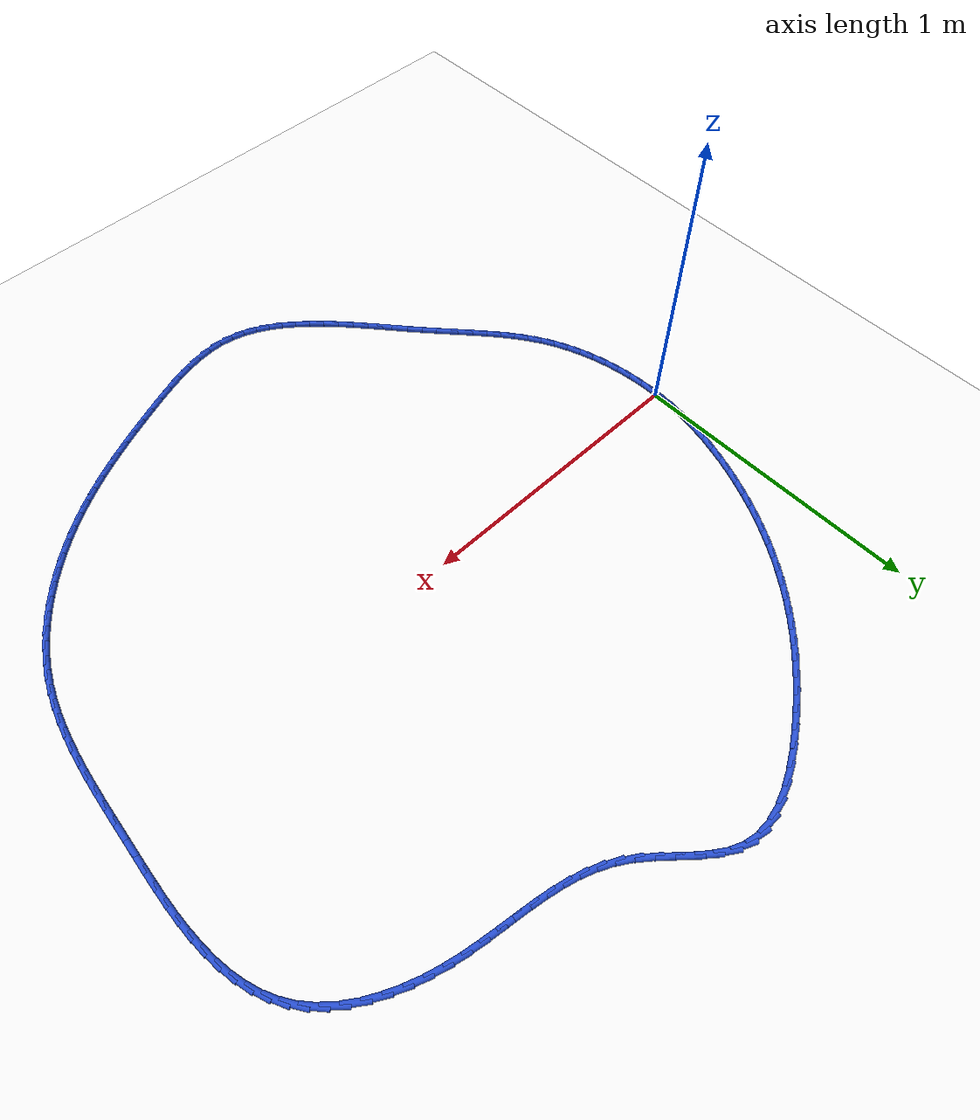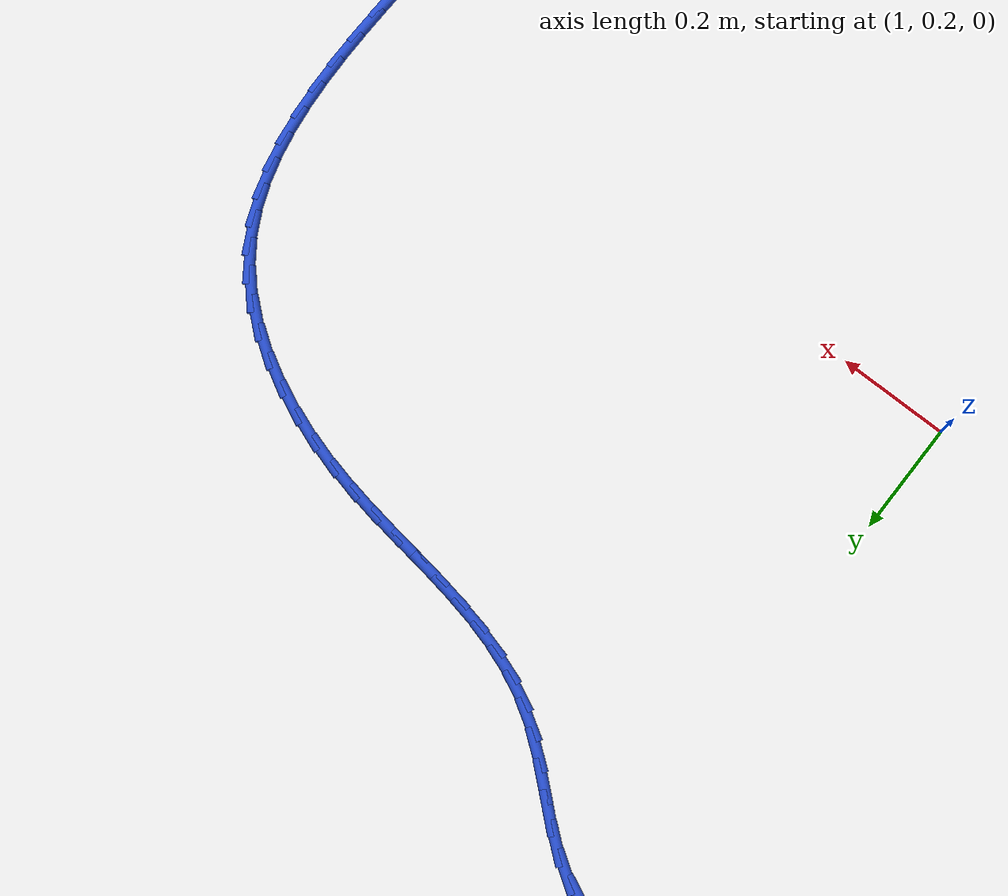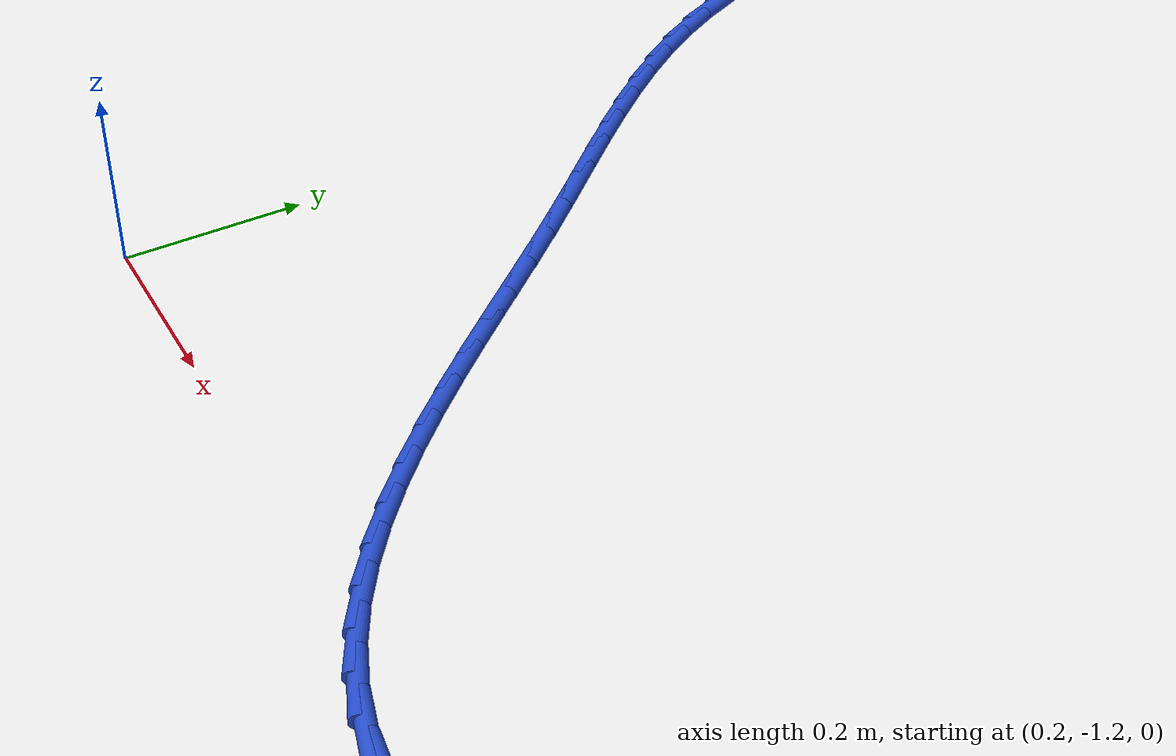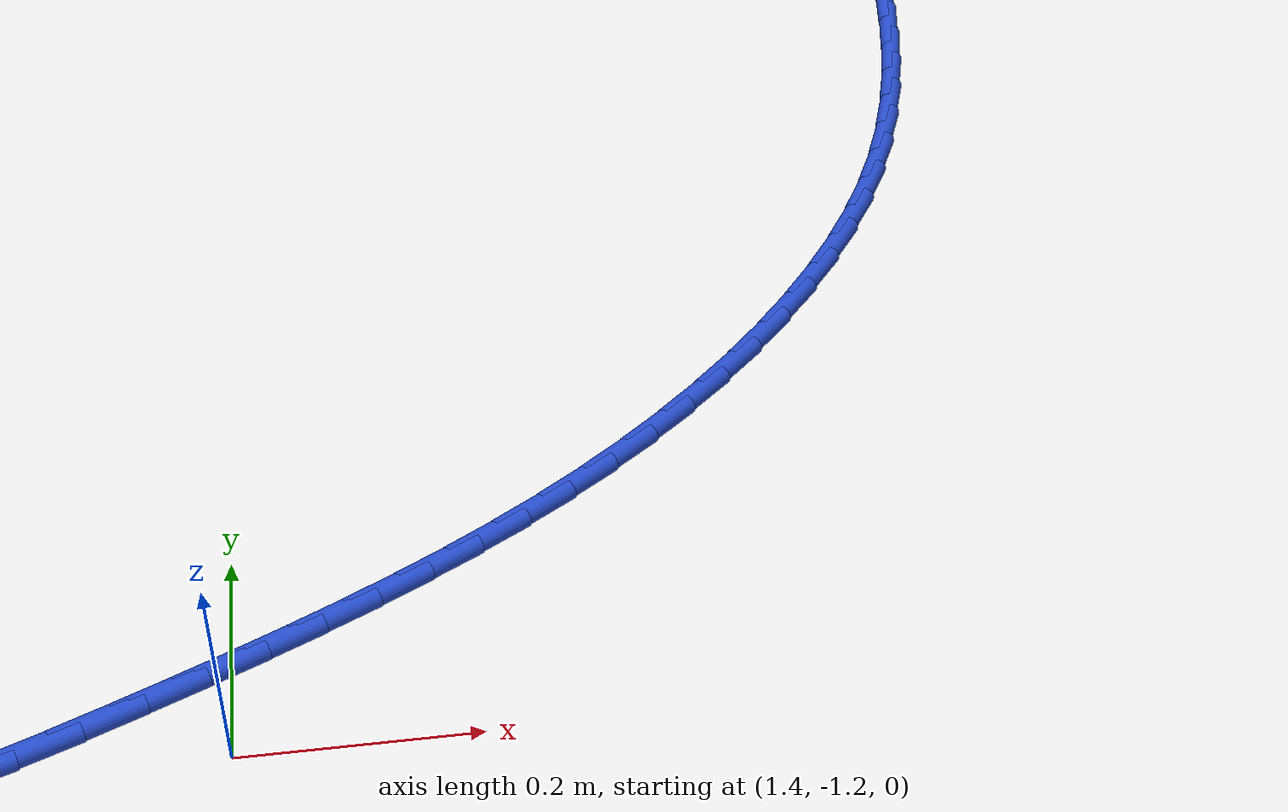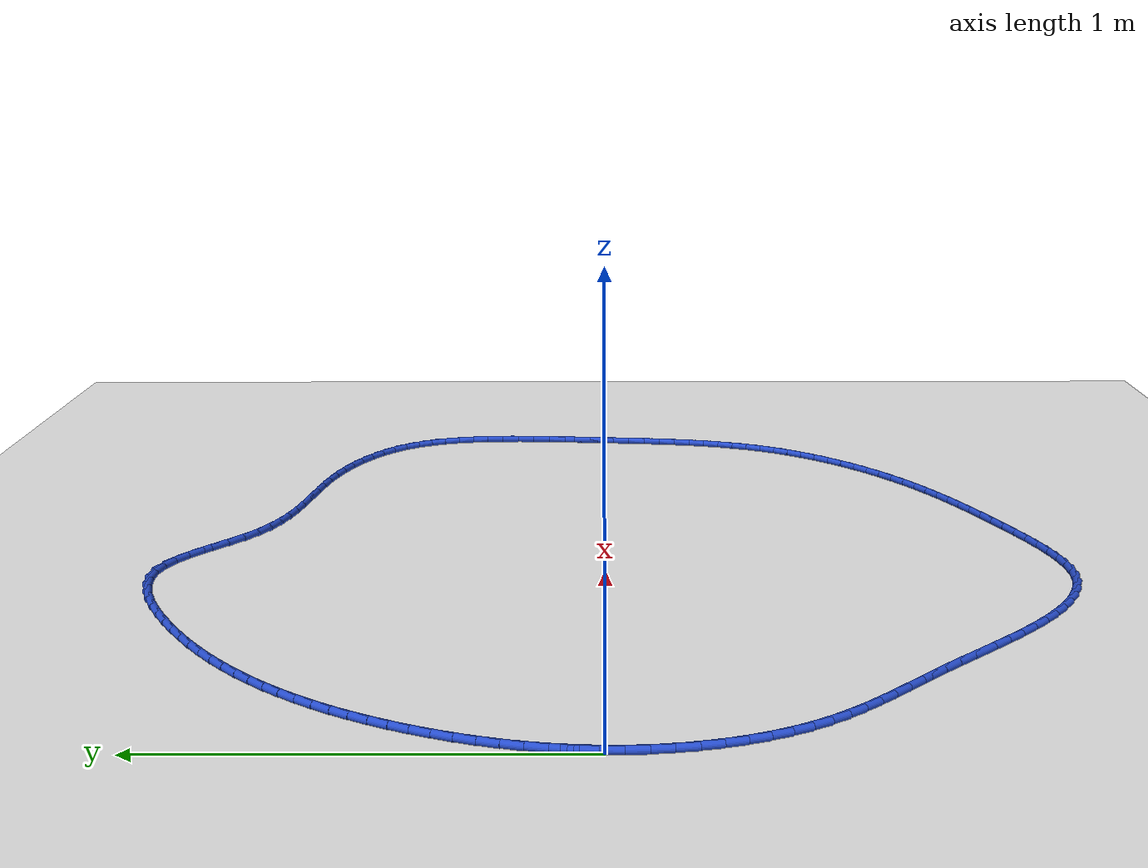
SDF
<sdf version="1.6">
 <world name="default">
  <light name="sun" type="directional">
   <pose>0 0 10 0 -0 0</pose>
   <diffuse>0.8 0.8 0.8 1</diffuse>
   <specular>0.2 0.2 0.2 1</specular>
   <attenuation>
    <range>1000</range>
    <constant>0.9</constant>
    <linear>0.01</linear>
    <quadratic>0.001</quadratic>
   </attenuation>
   <direction>-0.5 0.1 -0.9</direction>
  </light>
  <model name="ground_plane">
   <static>1</static>
   <link name="link">
    <collision name="collision">
     <geometry><plane><normal>0 0 1</normal><size>100 100</size></plane></geometry>
     <surface><friction><ode><mu>100</mu><mu2>50</mu2></ode></friction></surface>
    </collision>
    <visual name="visual">
     <cast_shadows>0</cast_shadows>
     <geometry><plane><normal>0 0 1</normal><size>100 100</size></plane></geometry>
     <material>
      <script><uri>file://media/materials/scripts/gazebo.material</uri><name>Gazebo/WhiteGlow</name></script>
     </material>
    </visual>
   </link>
  </model>
  <gravity>0 0 -9.8</gravity>
  <magnetic_field>6e-06 2.3e-05 -4.2e-05</magnetic_field>
  <atmosphere type="adiabatic"/>
  <physics name="default_physics" default="0" type="ode">
   <max_step_size>0.001</max_step_size>
   <real_time_factor>1</real_time_factor>
   <real_time_update_rate>1000</real_time_update_rate>
  </physics>
  <scene><ambient>0.4 0.4 0.4 1</ambient><background>0.7 0.7 0.7 1</background><shadows>1</shadows></scene>
  <spherical_coordinates>
   <surface_model>EARTH_WGS84</surface_model>
   <latitude_deg>0</latitude_deg>
   <longitude_deg>0</longitude_deg>
   <elevation>0</elevation>
   <heading_deg>0</heading_deg>
  </spherical_coordinates>
  <model name="line">
   <link name="link_0">
    <pose>3.469446951953614e-18 -1.1102230246251565e-16 0.01 0 1.57 1.524657564823388</pose>
    <collision name="collision">
     <geometry><cylinder><radius>0.01</radius><length>0.08</length></cylinder></geometry>
    </collision>
    <visual name="visual">
     <material>
      <script><name>Gazebo/Blue</name><uri>file://media/materials/scripts/gazebo.material</uri></script>
     </material>
     <geometry><cylinder><radius>0.01</radius><length>0.08</length></cylinder></geometry>
    </visual>
   </link>
   <link name="link_1">
    <pose>0.0023846333573592465 0.05164726774522099 0.01 0 1.57 1.4725105306670718</pose>
    <collision name="collision">
     <geometry><cylinder><radius>0.01</radius><length>0.08</length></cylinder></geometry>
    </collision>
    <visual name="visual">
     <material>
      <script><name>Gazebo/Blue</name><uri>file://media/materials/scripts/gazebo.material</uri></script>
     </material>
     <geometry><cylinder><radius>0.01</radius><length>0.08</length></cylinder></geometry>
    </visual>
   </link>
   <link name="link_2">
    <pose>0.007439835613251447 0.10291524384902694 0.01 0 1.57 1.423034019869949</pose>
    <collision name="collision">
     <geometry><cylinder><radius>0.01</radius><length>0.08</length></cylinder></geometry>
    </collision>
    <visual name="visual">
     <material>
      <script><name>Gazebo/Blue</name><uri>file://media/materials/scripts/gazebo.material</uri></script>
     </material>
     <geometry><cylinder><radius>0.01</radius><length>0.08</length></cylinder></geometry>
    </visual>
   </link>
   <link name="link_3">
    <pose>0.015004989862968705 0.153740218516599 0.01 0 1.57 1.3762527675569038</pose>
    <collision name="collision">
     <geometry><cylinder><radius>0.01</radius><length>0.08</length></cylinder></geometry>
    </collision>
    <visual name="visual">
     <material>
      <script><name>Gazebo/Blue</name><uri>file://media/materials/scripts/gazebo.material</uri></script>
     </material>
     <geometry><cylinder><radius>0.01</radius><length>0.08</length></cylinder></geometry>
    </visual>
   </link>
   <link name="link_4">
    <pose>0.024919479201803124 0.20405848195311835 0.01 0 1.57 1.332141817218762</pose>
    <collision name="collision">
     <geometry><cylinder><radius>0.01</radius><length>0.08</length></cylinder></geometry>
    </collision>
    <visual name="visual">
     <material>
      <script><name>Gazebo/Blue</name><uri>file://media/materials/scripts/gazebo.material</uri></script>
     </material>
     <geometry><cylinder><radius>0.01</radius><length>0.08</length></cylinder></geometry>
    </visual>
   </link>
   <link name="link_5">
    <pose>0.03702268672504682 0.25380632436376643 0.01 0 1.57 1.290637450865331</pose>
    <collision name="collision">
     <geometry><cylinder><radius>0.01</radius><length>0.08</length></cylinder></geometry>
    </collision>
    <visual name="visual">
     <material>
      <script><name>Gazebo/Blue</name><uri>file://media/materials/scripts/gazebo.material</uri></script>
     </material>
     <geometry><cylinder><radius>0.01</radius><length>0.08</length></cylinder></geometry>
    </visual>
   </link>
   <link name="link_6">
    <pose>0.051153995527991866 0.3029200359537244 0.01 0 1.57 1.251647321818144</pose>
    <collision name="collision">
     <geometry><cylinder><radius>0.01</radius><length>0.08</length></cylinder></geometry>
    </collision>
    <visual name="visual">
     <material>
      <script><name>Gazebo/Blue</name><uri>file://media/materials/scripts/gazebo.material</uri></script>
     </material>
     <geometry><cylinder><radius>0.01</radius><length>0.08</length></cylinder></geometry>
    </visual>
   </link>
   <link name="link_7">
    <pose>0.06715278870593037 0.35133590692817346 0.01 0 1.57 1.215059310888163</pose>
    <collision name="collision">
     <geometry><cylinder><radius>0.01</radius><length>0.08</length></cylinder></geometry>
    </collision>
    <visual name="visual">
     <material>
      <script><name>Gazebo/Blue</name><uri>file://media/materials/scripts/gazebo.material</uri></script>
     </material>
     <geometry><cylinder><radius>0.01</radius><length>0.08</length></cylinder></geometry>
    </visual>
   </link>
   <link name="link_8">
    <pose>0.08485844935415449 0.39899022749229507 0.01 0 1.57 1.180740380777531</pose>
    <collision name="collision">
     <geometry><cylinder><radius>0.01</radius><length>0.08</length></cylinder></geometry>
    </collision>
    <visual name="visual">
     <material>
      <script><name>Gazebo/Blue</name><uri>file://media/materials/scripts/gazebo.material</uri></script>
     </material>
     <geometry><cylinder><radius>0.01</radius><length>0.08</length></cylinder></geometry>
    </visual>
   </link>
   <link name="link_9">
    <pose>0.10411089035153306 0.44581944089820025 0.01 0 1.57 1.1476138869905304</pose>
    <collision name="collision">
     <geometry><cylinder><radius>0.01</radius><length>0.08</length></cylinder></geometry>
    </collision>
    <visual name="visual">
     <material>
      <script><name>Gazebo/Blue</name><uri>file://media/materials/scripts/gazebo.material</uri></script>
     </material>
     <geometry><cylinder><radius>0.01</radius><length>0.08</length></cylinder></geometry>
    </visual>
   </link>
   <link name="link_10">
    <pose>0.12481010590435052 0.49177734703776405 0.01 0 1.57 1.1138477608017856</pose>
    <collision name="collision">
     <geometry><cylinder><radius>0.01</radius><length>0.08</length></cylinder></geometry>
    </collision>
    <visual name="visual">
     <material>
      <script><name>Gazebo/Blue</name><uri>file://media/materials/scripts/gazebo.material</uri></script>
     </material>
     <geometry><cylinder><radius>0.01</radius><length>0.08</length></cylinder></geometry>
    </visual>
   </link>
   <link name="link_11">
    <pose>0.14697067383011767 0.536850847376155 0.01 0 1.57 1.0793095955290892</pose>
    <collision name="collision">
     <geometry><cylinder><radius>0.01</radius><length>0.08</length></cylinder></geometry>
    </collision>
    <visual name="visual">
     <material>
      <script><name>Gazebo/Blue</name><uri>file://media/materials/scripts/gazebo.material</uri></script>
     </material>
     <geometry><cylinder><radius>0.01</radius><length>0.08</length></cylinder></geometry>
    </visual>
   </link>
   <link name="link_12">
    <pose>0.17062004800832628 0.5810305630894561 0.01 0 1.57 1.0440853340766052</pose>
    <collision name="collision">
     <geometry><cylinder><radius>0.01</radius><length>0.08</length></cylinder></geometry>
    </collision>
    <visual name="visual">
     <material>
      <script><name>Gazebo/Blue</name><uri>file://media/materials/scripts/gazebo.material</uri></script>
     </material>
     <geometry><cylinder><radius>0.01</radius><length>0.08</length></cylinder></geometry>
    </visual>
   </link>
   <link name="link_13">
    <pose>0.19578568231846805 0.6243071153537505 0.01 0 1.57 1.008271320992604</pose>
    <collision name="collision">
     <geometry><cylinder><radius>0.01</radius><length>0.08</length></cylinder></geometry>
    </collision>
    <visual name="visual">
     <material>
      <script><name>Gazebo/Blue</name><uri>file://media/materials/scripts/gazebo.material</uri></script>
     </material>
     <geometry><cylinder><radius>0.01</radius><length>0.08</length></cylinder></geometry>
    </visual>
   </link>
   <link name="link_14">
    <pose>0.22249503064003473 0.6666711253451216 0.01 0 1.57 0.9719732042534099</pose>
    <collision name="collision">
     <geometry><cylinder><radius>0.01</radius><length>0.08</length></cylinder></geometry>
    </collision>
    <visual name="visual">
     <material>
      <script><name>Gazebo/Blue</name><uri>file://media/materials/scripts/gazebo.material</uri></script>
     </material>
     <geometry><cylinder><radius>0.01</radius><length>0.08</length></cylinder></geometry>
    </visual>
   </link>
   <link name="link_15">
    <pose>0.2507755468525181 0.7081132142396527 0.01 0 1.57 0.9353044651488828</pose>
    <collision name="collision">
     <geometry><cylinder><radius>0.01</radius><length>0.08</length></cylinder></geometry>
    </collision>
    <visual name="visual">
     <material>
      <script><name>Gazebo/Blue</name><uri>file://media/materials/scripts/gazebo.material</uri></script>
     </material>
     <geometry><cylinder><radius>0.01</radius><length>0.08</length></cylinder></geometry>
    </visual>
   </link>
   <link name="link_16">
    <pose>0.28065468483540995 0.748624003213427 0.01 0 1.57 0.8983846157877549</pose>
    <collision name="collision">
     <geometry><cylinder><radius>0.01</radius><length>0.08</length></cylinder></geometry>
    </collision>
    <visual name="visual">
     <material>
      <script><name>Gazebo/Blue</name><uri>file://media/materials/scripts/gazebo.material</uri></script>
     </material>
     <geometry><cylinder><radius>0.01</radius><length>0.08</length></cylinder></geometry>
    </visual>
   </link>
   <link name="link_17">
    <pose>0.31215989846820197 0.7881941134425278 0.01 0 1.57 0.8613371289141685</pose>
    <collision name="collision">
     <geometry><cylinder><radius>0.01</radius><length>0.08</length></cylinder></geometry>
    </collision>
    <visual name="visual">
     <material>
      <script><name>Gazebo/Blue</name><uri>file://media/materials/scripts/gazebo.material</uri></script>
     </material>
     <geometry><cylinder><radius>0.01</radius><length>0.08</length></cylinder></geometry>
    </visual>
   </link>
   <link name="link_18">
    <pose>0.3453186416303858 0.826814166103038 0.01 0 1.57 0.8242871862611012</pose>
    <collision name="collision">
     <geometry><cylinder><radius>0.01</radius><length>0.08</length></cylinder></geometry>
    </collision>
    <visual name="visual">
     <material>
      <script><name>Gazebo/Blue</name><uri>file://media/materials/scripts/gazebo.material</uri></script>
     </material>
     <geometry><cylinder><radius>0.01</radius><length>0.08</length></cylinder></geometry>
    </visual>
   </link>
   <link name="link_19">
    <pose>0.3801583682014533 0.8644747823710415 0.01 0 1.57 0.7873593468600117</pose>
    <collision name="collision">
     <geometry><cylinder><radius>0.01</radius><length>0.08</length></cylinder></geometry>
    </collision>
    <visual name="visual">
     <material>
      <script><name>Gazebo/Blue</name><uri>file://media/materials/scripts/gazebo.material</uri></script>
     </material>
     <geometry><cylinder><radius>0.01</radius><length>0.08</length></cylinder></geometry>
    </visual>
   </link>
   <link name="link_20">
    <pose>0.4167065320608964 0.9011665834226212 0.01 0 1.57 0.7506752435736888</pose>
    <collision name="collision">
     <geometry><cylinder><radius>0.01</radius><length>0.08</length></cylinder></geometry>
    </collision>
    <visual name="visual">
     <material>
      <script><name>Gazebo/Blue</name><uri>file://media/materials/scripts/gazebo.material</uri></script>
     </material>
     <geometry><cylinder><radius>0.01</radius><length>0.08</length></cylinder></geometry>
    </visual>
   </link>
   <link name="link_21">
    <pose>0.4549905870882065 0.9368801904338604 0.01 0 1.57 0.7143514136931837</pose>
    <collision name="collision">
     <geometry><cylinder><radius>0.01</radius><length>0.08</length></cylinder></geometry>
    </collision>
    <visual name="visual">
     <material>
      <script><name>Gazebo/Blue</name><uri>file://media/materials/scripts/gazebo.material</uri></script>
     </material>
     <geometry><cylinder><radius>0.01</radius><length>0.08</length></cylinder></geometry>
    </visual>
   </link>
   <link name="link_22">
    <pose>0.4950379871628757 0.9716062245808422 0.01 0 1.57 0.6784973580704299</pose>
    <collision name="collision">
     <geometry><cylinder><radius>0.01</radius><length>0.08</length></cylinder></geometry>
    </collision>
    <visual name="visual">
     <material>
      <script><name>Gazebo/Blue</name><uri>file://media/materials/scripts/gazebo.material</uri></script>
     </material>
     <geometry><cylinder><radius>0.01</radius><length>0.08</length></cylinder></geometry>
    </visual>
   </link>
   <link name="link_23">
    <pose>0.5368761861643954 1.0053353070396502 0.01 0 1.57 0.6432139044689602</pose>
    <collision name="collision">
     <geometry><cylinder><radius>0.01</radius><length>0.08</length></cylinder></geometry>
    </collision>
    <visual name="visual">
     <material>
      <script><name>Gazebo/Blue</name><uri>file://media/materials/scripts/gazebo.material</uri></script>
     </material>
     <geometry><cylinder><radius>0.01</radius><length>0.08</length></cylinder></geometry>
    </visual>
   </link>
   <link name="link_24">
    <pose>0.5805326379722575 1.0380580589863673 0.01 0 1.57 0.6085919270302591</pose>
    <collision name="collision">
     <geometry><cylinder><radius>0.01</radius><length>0.08</length></cylinder></geometry>
    </collision>
    <visual name="visual">
     <material>
      <script><name>Gazebo/Blue</name><uri>file://media/materials/scripts/gazebo.material</uri></script>
     </material>
     <geometry><cylinder><radius>0.01</radius><length>0.08</length></cylinder></geometry>
    </visual>
   </link>
   <link name="link_25">
    <pose>0.6260347964659538 1.0697651015970766 0.01 0 1.57 0.5744846938816968</pose>
    <collision name="collision">
     <geometry><cylinder><radius>0.01</radius><length>0.08</length></cylinder></geometry>
    </collision>
    <visual name="visual">
     <material>
      <script><name>Gazebo/Blue</name><uri>file://media/materials/scripts/gazebo.material</uri></script>
     </material>
     <geometry><cylinder><radius>0.01</radius><length>0.08</length></cylinder></geometry>
    </visual>
   </link>
   <link name="link_26">
    <pose>0.673399442512721 1.1004249011869518 0.01 0 1.57 0.5342905004151267</pose>
    <collision name="collision">
     <geometry><cylinder><radius>0.01</radius><length>0.08</length></cylinder></geometry>
    </collision>
    <visual name="visual">
     <material>
      <script><name>Gazebo/Blue</name><uri>file://media/materials/scripts/gazebo.material</uri></script>
     </material>
     <geometry><cylinder><radius>0.01</radius><length>0.08</length></cylinder></geometry>
    </visual>
   </link>
   <link name="link_27">
    <pose>0.7223444225763069 1.1293854010199205 0.01 0 1.57 0.4789846975595859</pose>
    <collision name="collision">
     <geometry><cylinder><radius>0.01</radius><length>0.08</length></cylinder></geometry>
    </collision>
    <visual name="visual">
     <material>
      <script><name>Gazebo/Blue</name><uri>file://media/materials/scripts/gazebo.material</uri></script>
     </material>
     <geometry><cylinder><radius>0.01</radius><length>0.08</length></cylinder></geometry>
    </visual>
   </link>
   <link name="link_28">
    <pose>0.7722555397671594 1.1553052943026003 0.01 0 1.57 0.40435603368860207</pose>
    <collision name="collision">
     <geometry><cylinder><radius>0.01</radius><length>0.08</length></cylinder></geometry>
    </collision>
    <visual name="visual">
     <material>
      <script><name>Gazebo/Blue</name><uri>file://media/materials/scripts/gazebo.material</uri></script>
     </material>
     <geometry><cylinder><radius>0.01</radius><length>0.08</length></cylinder></geometry>
    </visual>
   </link>
   <link name="link_29">
    <pose>0.8225012794813981 1.176807326418911 0.01 0 1.57 0.304669524520477</pose>
    <collision name="collision">
     <geometry><cylinder><radius>0.01</radius><length>0.08</length></cylinder></geometry>
    </collision>
    <visual name="visual">
     <material>
      <script><name>Gazebo/Blue</name><uri>file://media/materials/scripts/gazebo.material</uri></script>
     </material>
     <geometry><cylinder><radius>0.01</radius><length>0.08</length></cylinder></geometry>
    </visual>
   </link>
   <link name="link_30">
    <pose>0.8724501271151436 1.1925142427527737 0.01 0 1.57 0.17237400252887308</pose>
    <collision name="collision">
     <geometry><cylinder><radius>0.01</radius><length>0.08</length></cylinder></geometry>
    </collision>
    <visual name="visual">
     <material>
      <script><name>Gazebo/Blue</name><uri>file://media/materials/scripts/gazebo.material</uri></script>
     </material>
     <geometry><cylinder><radius>0.01</radius><length>0.08</length></cylinder></geometry>
    </visual>
   </link>
   <link name="link_31">
    <pose>0.9214705680645162 1.201048788688109 0.01 0 1.57 -0.0003177183661695332</pose>
    <collision name="collision">
     <geometry><cylinder><radius>0.01</radius><length>0.08</length></cylinder></geometry>
    </collision>
    <visual name="visual">
     <material>
      <script><name>Gazebo/Blue</name><uri>file://media/materials/scripts/gazebo.material</uri></script>
     </material>
     <geometry><cylinder><radius>0.01</radius><length>0.08</length></cylinder></geometry>
    </visual>
   </link>
   <link name="link_32">
    <pose>0.9689310877256362 1.2010337096088373 0.01 0 1.57 -0.21611326726454302</pose>
    <collision name="collision">
     <geometry><cylinder><radius>0.01</radius><length>0.08</length></cylinder></geometry>
    </collision>
    <visual name="visual">
     <material>
      <script><name>Gazebo/Blue</name><uri>file://media/materials/scripts/gazebo.material</uri></script>
     </material>
     <geometry><cylinder><radius>0.01</radius><length>0.08</length></cylinder></geometry>
    </visual>
   </link>
   <link name="link_33">
    <pose>1.014201276463728 1.1910950084566505 0.01 0 1.57 -0.44000558929535444</pose>
    <collision name="collision">
     <geometry><cylinder><radius>0.01</radius><length>0.08</length></cylinder></geometry>
    </collision>
    <visual name="visual">
     <material>
      <script><name>Gazebo/Blue</name><uri>file://media/materials/scripts/gazebo.material</uri></script>
     </material>
     <geometry><cylinder><radius>0.01</radius><length>0.08</length></cylinder></geometry>
    </visual>
   </link>
   <link name="link_34">
    <pose>1.057016825440138 1.170937989385309 0.01 0 1.57 -0.5998741035629457</pose>
    <collision name="collision">
     <geometry><cylinder><radius>0.01</radius><length>0.08</length></cylinder></geometry>
    </collision>
    <visual name="visual">
     <material>
      <script><name>Gazebo/Blue</name><uri>file://media/materials/scripts/gazebo.material</uri></script>
     </material>
     <geometry><cylinder><radius>0.01</radius><length>0.08</length></cylinder></geometry>
    </visual>
   </link>
   <link name="link_35">
    <pose>1.0980071035580776 1.1429026065690335 0.01 0 1.57 -0.6933448418020439</pose>
    <collision name="collision">
     <geometry><cylinder><radius>0.01</radius><length>0.08</length></cylinder></geometry>
    </collision>
    <visual name="visual">
     <material>
      <script><name>Gazebo/Blue</name><uri>file://media/materials/scripts/gazebo.material</uri></script>
     </material>
     <geometry><cylinder><radius>0.01</radius><length>0.08</length></cylinder></geometry>
    </visual>
   </link>
   <link name="link_36">
    <pose>1.1379352854605909 1.1097232866844626 0.01 0 1.57 -0.7317335381845154</pose>
    <collision name="collision">
     <geometry><cylinder><radius>0.01</radius><length>0.08</length></cylinder></geometry>
    </collision>
    <visual name="visual">
     <material>
      <script><name>Gazebo/Blue</name><uri>file://media/materials/scripts/gazebo.material</uri></script>
     </material>
     <geometry><cylinder><radius>0.01</radius><length>0.08</length></cylinder></geometry>
    </visual>
   </link>
   <link name="link_37">
    <pose>1.1775645457907205 1.0741344564082316 0.01 0 1.57 -0.7213964662566799</pose>
    <collision name="collision">
     <geometry><cylinder><radius>0.01</radius><length>0.08</length></cylinder></geometry>
    </collision>
    <visual name="visual">
     <material>
      <script><name>Gazebo/Blue</name><uri>file://media/materials/scripts/gazebo.material</uri></script>
     </material>
     <geometry><cylinder><radius>0.01</radius><length>0.08</length></cylinder></geometry>
    </visual>
   </link>
   <link name="link_38">
    <pose>1.2176580591915096 1.0388705424169773 0.01 0 1.57 -0.6620385328162225</pose>
    <collision name="collision">
     <geometry><cylinder><radius>0.01</radius><length>0.08</length></cylinder></geometry>
    </collision>
    <visual name="visual">
     <material>
      <script><name>Gazebo/Blue</name><uri>file://media/materials/scripts/gazebo.material</uri></script>
     </material>
     <geometry><cylinder><radius>0.01</radius><length>0.08</length></cylinder></geometry>
    </visual>
   </link>
   <link name="link_39">
    <pose>1.2589790003060026 1.0066659713873365 0.01 0 1.57 -0.555360376780421</pose>
    <collision name="collision">
     <geometry><cylinder><radius>0.01</radius><length>0.08</length></cylinder></geometry>
    </collision>
    <visual name="visual">
     <material>
      <script><name>Gazebo/Blue</name><uri>file://media/materials/scripts/gazebo.material</uri></script>
     </material>
     <geometry><cylinder><radius>0.01</radius><length>0.08</length></cylinder></geometry>
    </visual>
   </link>
   <link name="link_40">
    <pose>1.302181574808645 0.979858560709502 0.01 0 1.57 -0.44366950882743483</pose>
    <collision name="collision">
     <geometry><cylinder><radius>0.01</radius><length>0.08</length></cylinder></geometry>
    </collision>
    <visual name="visual">
     <material>
      <script><name>Gazebo/Blue</name><uri>file://media/materials/scripts/gazebo.material</uri></script>
     </material>
     <geometry><cylinder><radius>0.01</radius><length>0.08</length></cylinder></geometry>
    </visual>
   </link>
   <link name="link_41">
    <pose>1.3472721725349095 0.9584283025969158 0.01 0 1.57 -0.3476788431000535</pose>
    <collision name="collision">
     <geometry><cylinder><radius>0.01</radius><length>0.08</length></cylinder></geometry>
    </collision>
    <visual name="visual">
     <material>
      <script><name>Gazebo/Blue</name><uri>file://media/materials/scripts/gazebo.material</uri></script>
     </material>
     <geometry><cylinder><radius>0.01</radius><length>0.08</length></cylinder></geometry>
    </visual>
   </link>
   <link name="link_42">
    <pose>1.3940187388656822 0.9414873340726139 0.01 0 1.57 -0.2701817047731345</pose>
    <collision name="collision">
     <geometry><cylinder><radius>0.01</radius><length>0.08</length></cylinder></geometry>
    </collision>
    <visual name="visual">
     <material>
      <script><name>Gazebo/Blue</name><uri>file://media/materials/scripts/gazebo.material</uri></script>
     </material>
     <geometry><cylinder><radius>0.01</radius><length>0.08</length></cylinder></geometry>
    </visual>
   </link>
   <link name="link_43">
    <pose>1.4421888479101332 0.9281464408592379 0.01 0 1.57 -0.21211245688839725</pose>
    <collision name="collision">
     <geometry><cylinder><radius>0.01</radius><length>0.08</length></cylinder></geometry>
    </collision>
    <visual name="visual">
     <material>
      <script><name>Gazebo/Blue</name><uri>file://media/materials/scripts/gazebo.material</uri></script>
     </material>
     <geometry><cylinder><radius>0.01</radius><length>0.08</length></cylinder></geometry>
    </visual>
   </link>
   <link name="link_44">
    <pose>1.491550073777433 0.9175164086794299 0.01 0 1.57 -0.17329194334510015</pose>
    <collision name="collision">
     <geometry><cylinder><radius>0.01</radius><length>0.08</length></cylinder></geometry>
    </collision>
    <visual name="visual">
     <material>
      <script><name>Gazebo/Blue</name><uri>file://media/materials/scripts/gazebo.material</uri></script>
     </material>
     <geometry><cylinder><radius>0.01</radius><length>0.08</length></cylinder></geometry>
    </visual>
   </link>
   <link name="link_45">
    <pose>1.5418699905767514 0.9087080232558314 0.01 0 1.57 -0.15308360173952398</pose>
    <collision name="collision">
     <geometry><cylinder><radius>0.01</radius><length>0.08</length></cylinder></geometry>
    </collision>
    <visual name="visual">
     <material>
      <script><name>Gazebo/Blue</name><uri>file://media/materials/scripts/gazebo.material</uri></script>
     </material>
     <geometry><cylinder><radius>0.01</radius><length>0.08</length></cylinder></geometry>
    </visual>
   </link>
   <link name="link_46">
    <pose>1.5929161724172591 0.9008320703110849 0.01 0 1.57 -0.1508197892313906</pose>
    <collision name="collision">
     <geometry><cylinder><radius>0.01</radius><length>0.08</length></cylinder></geometry>
    </collision>
    <visual name="visual">
     <material>
      <script><name>Gazebo/Blue</name><uri>file://media/materials/scripts/gazebo.material</uri></script>
     </material>
     <geometry><cylinder><radius>0.01</radius><length>0.08</length></cylinder></geometry>
    </visual>
   </link>
   <link name="link_47">
    <pose>1.6444561934081265 0.8929993355678326 0.01 0 1.57 -0.16599675672338854</pose>
    <collision name="collision">
     <geometry><cylinder><radius>0.01</radius><length>0.08</length></cylinder></geometry>
    </collision>
    <visual name="visual">
     <material>
      <script><name>Gazebo/Blue</name><uri>file://media/materials/scripts/gazebo.material</uri></script>
     </material>
     <geometry><cylinder><radius>0.01</radius><length>0.08</length></cylinder></geometry>
    </visual>
   </link>
   <link name="link_48">
    <pose>1.696257627658524 0.8843206047487155 0.01 0 1.57 -0.19828322422897765</pose>
    <collision name="collision">
     <geometry><cylinder><radius>0.01</radius><length>0.08</length></cylinder></geometry>
    </collision>
    <visual name="visual">
     <material>
      <script><name>Gazebo/Blue</name><uri>file://media/materials/scripts/gazebo.material</uri></script>
     </material>
     <geometry><cylinder><radius>0.01</radius><length>0.08</length></cylinder></geometry>
    </visual>
   </link>
   <link name="link_49">
    <pose>1.7480880492776214 0.8739066635763767 0.01 0 1.57 -0.24736332747238596</pose>
    <collision name="collision">
     <geometry><cylinder><radius>0.01</radius><length>0.08</length></cylinder></geometry>
    </collision>
    <visual name="visual">
     <material>
      <script><name>Gazebo/Blue</name><uri>file://media/materials/scripts/gazebo.material</uri></script>
     </material>
     <geometry><cylinder><radius>0.01</radius><length>0.08</length></cylinder></geometry>
    </visual>
   </link>
   <link name="link_50">
    <pose>1.7997145126319094 0.8608691631876783 0.01 0 1.57 -0.30928013860784875</pose>
    <collision name="collision">
     <geometry><cylinder><radius>0.01</radius><length>0.08</length></cylinder></geometry>
    </collision>
    <visual name="visual">
     <material>
      <script><name>Gazebo/Blue</name><uri>file://media/materials/scripts/gazebo.material</uri></script>
     </material>
     <geometry><cylinder><radius>0.01</radius><length>0.08</length></cylinder></geometry>
    </visual>
   </link>
   <link name="link_51">
    <pose>1.850760929131967 0.8445580994895641 0.01 0 1.57 -0.3765459851116786</pose>
    <collision name="collision">
     <geometry><cylinder><radius>0.01</radius><length>0.08</length></cylinder></geometry>
    </collision>
    <visual name="visual">
     <material>
      <script><name>Gazebo/Blue</name><uri>file://media/materials/scripts/gazebo.material</uri></script>
     </material>
     <geometry><cylinder><radius>0.01</radius><length>0.08</length></cylinder></geometry>
    </visual>
   </link>
   <link name="link_52">
    <pose>1.900513899092529 0.8248851190484529 0.01 0 1.57 -0.4500314156725472</pose>
    <collision name="collision">
     <geometry><cylinder><radius>0.01</radius><length>0.08</length></cylinder></geometry>
    </collision>
    <visual name="visual">
     <material>
      <script><name>Gazebo/Blue</name><uri>file://media/materials/scripts/gazebo.material</uri></script>
     </material>
     <geometry><cylinder><radius>0.01</radius><length>0.08</length></cylinder></geometry>
    </visual>
   </link>
   <link name="link_53">
    <pose>1.9482114659408634 0.8018427196337107 0.01 0 1.57 -0.5320418170914659</pose>
    <collision name="collision">
     <geometry><cylinder><radius>0.01</radius><length>0.08</length></cylinder></geometry>
    </collision>
    <visual name="visual">
     <material>
      <script><name>Gazebo/Blue</name><uri>file://media/materials/scripts/gazebo.material</uri></script>
     </material>
     <geometry><cylinder><radius>0.01</radius><length>0.08</length></cylinder></geometry>
    </visual>
   </link>
   <link name="link_54">
    <pose>1.9930916731042376 0.7754233990147016 0.01 0 1.57 -0.6250922533946844</pose>
    <collision name="collision">
     <geometry><cylinder><radius>0.01</radius><length>0.08</length></cylinder></geometry>
    </collision>
    <visual name="visual">
     <material>
      <script><name>Gazebo/Blue</name><uri>file://media/materials/scripts/gazebo.material</uri></script>
     </material>
     <geometry><cylinder><radius>0.01</radius><length>0.08</length></cylinder></geometry>
    </visual>
   </link>
   <link name="link_55">
    <pose>2.0343925640099223 0.7456196549607904 0.01 0 1.57 -0.7317978833888765</pose>
    <collision name="collision">
     <geometry><cylinder><radius>0.01</radius><length>0.08</length></cylinder></geometry>
    </collision>
    <visual name="visual">
     <material>
      <script><name>Gazebo/Blue</name><uri>file://media/materials/scripts/gazebo.material</uri></script>
     </material>
     <geometry><cylinder><radius>0.01</radius><length>0.08</length></cylinder></geometry>
    </visual>
   </link>
   <link name="link_56">
    <pose>2.0713521820851852 0.7124239852413429 0.01 0 1.57 -0.8545079864817634</pose>
    <collision name="collision">
     <geometry><cylinder><radius>0.01</radius><length>0.08</length></cylinder></geometry>
    </collision>
    <visual name="visual">
     <material>
      <script><name>Gazebo/Blue</name><uri>file://media/materials/scripts/gazebo.material</uri></script>
     </material>
     <geometry><cylinder><radius>0.01</radius><length>0.08</length></cylinder></geometry>
    </visual>
   </link>
   <link name="link_57">
    <pose>2.103208943885877 0.6758289885862514 0.01 0 1.57 -0.988533576709642</pose>
    <collision name="collision">
     <geometry><cylinder><radius>0.01</radius><length>0.08</length></cylinder></geometry>
    </collision>
    <visual name="visual">
     <material>
      <script><name>Gazebo/Blue</name><uri>file://media/materials/scripts/gazebo.material</uri></script>
     </material>
     <geometry><cylinder><radius>0.01</radius><length>0.08</length></cylinder></geometry>
    </visual>
   </link>
   <link name="link_58">
    <pose>2.1294941867470123 0.6359065217563946 0.01 0 1.57 -1.1149157498152207</pose>
    <collision name="collision">
     <geometry><cylinder><radius>0.01</radius><length>0.08</length></cylinder></geometry>
    </collision>
    <visual name="visual">
     <material>
      <script><name>Gazebo/Blue</name><uri>file://media/materials/scripts/gazebo.material</uri></script>
     </material>
     <geometry><cylinder><radius>0.01</radius><length>0.08</length></cylinder></geometry>
    </visual>
   </link>
   <link name="link_59">
    <pose>2.1505571238125283 0.5929497410271088 0.01 0 1.57 -1.2272970244718164</pose>
    <collision name="collision">
     <geometry><cylinder><radius>0.01</radius><length>0.08</length></cylinder></geometry>
    </collision>
    <visual name="visual">
     <material>
      <script><name>Gazebo/Blue</name><uri>file://media/materials/scripts/gazebo.material</uri></script>
     </material>
     <geometry><cylinder><radius>0.01</radius><length>0.08</length></cylinder></geometry>
    </visual>
   </link>
   <link name="link_60">
    <pose>2.166888606336506 0.5472901268846483 0.01 0 1.57 -1.3241892328773903</pose>
    <collision name="collision">
     <geometry><cylinder><radius>0.01</radius><length>0.08</length></cylinder></geometry>
    </collision>
    <visual name="visual">
     <material>
      <script><name>Gazebo/Blue</name><uri>file://media/materials/scripts/gazebo.material</uri></script>
     </material>
     <geometry><cylinder><radius>0.01</radius><length>0.08</length></cylinder></geometry>
    </visual>
   </link>
   <link name="link_61">
    <pose>2.178979485573028 0.49925915981526603 0.01 0 1.57 -1.405725625188175</pose>
    <collision name="collision">
     <geometry><cylinder><radius>0.01</radius><length>0.08</length></cylinder></geometry>
    </collision>
    <visual name="visual">
     <material>
      <script><name>Gazebo/Blue</name><uri>file://media/materials/scripts/gazebo.material</uri></script>
     </material>
     <geometry><cylinder><radius>0.01</radius><length>0.08</length></cylinder></geometry>
    </visual>
   </link>
   <link name="link_62">
    <pose>2.187320612776176 0.449188320305216 0.01 0 1.57 -1.4729578765458293</pose>
    <collision name="collision">
     <geometry><cylinder><radius>0.01</radius><length>0.08</length></cylinder></geometry>
    </collision>
    <visual name="visual">
     <material>
      <script><name>Gazebo/Blue</name><uri>file://media/materials/scripts/gazebo.material</uri></script>
     </material>
     <geometry><cylinder><radius>0.01</radius><length>0.08</length></cylinder></geometry>
    </visual>
   </link>
   <link name="link_63">
    <pose>2.192402839200033 0.39740908884075116 0.01 0 1.57 -1.527288344764262</pose>
    <collision name="collision">
     <geometry><cylinder><radius>0.01</radius><length>0.08</length></cylinder></geometry>
    </collision>
    <visual name="visual">
     <material>
      <script><name>Gazebo/Blue</name><uri>file://media/materials/scripts/gazebo.material</uri></script>
     </material>
     <geometry><cylinder><radius>0.01</radius><length>0.08</length></cylinder></geometry>
    </visual>
   </link>
   <link name="link_64">
    <pose>2.19471701609868 0.3442529459081258 0.01 0 1.57 -1.5701140842120487</pose>
    <collision name="collision">
     <geometry><cylinder><radius>0.01</radius><length>0.08</length></cylinder></geometry>
    </collision>
    <visual name="visual">
     <material>
      <script><name>Gazebo/Blue</name><uri>file://media/materials/scripts/gazebo.material</uri></script>
     </material>
     <geometry><cylinder><radius>0.01</radius><length>0.08</length></cylinder></geometry>
    </visual>
   </link>
   <link name="link_65">
    <pose>2.194753994726199 0.290051371993593 0.01 0 1.57 1.538951470054085</pose>
    <collision name="collision">
     <geometry><cylinder><radius>0.01</radius><length>0.08</length></cylinder></geometry>
    </collision>
    <visual name="visual">
     <material>
      <script><name>Gazebo/Blue</name><uri>file://media/materials/scripts/gazebo.material</uri></script>
     </material>
     <geometry><cylinder><radius>0.01</radius><length>0.08</length></cylinder></geometry>
    </visual>
   </link>
   <link name="link_66">
    <pose>2.1930046263366734 0.23513584758340586 0.01 0 1.57 1.5157890428336511</pose>
    <collision name="collision">
     <geometry><cylinder><radius>0.01</radius><length>0.08</length></cylinder></geometry>
    </collision>
    <visual name="visual">
     <material>
      <script><name>Gazebo/Blue</name><uri>file://media/materials/scripts/gazebo.material</uri></script>
     </material>
     <geometry><cylinder><radius>0.01</radius><length>0.08</length></cylinder></geometry>
    </visual>
   </link>
   <link name="link_67">
    <pose>2.189959762184184 0.17983785316381887 0.01 0 1.57 1.5013583817521574</pose>
    <collision name="collision">
     <geometry><cylinder><radius>0.01</radius><length>0.08</length></cylinder></geometry>
    </collision>
    <visual name="visual">
     <material>
      <script><name>Gazebo/Blue</name><uri>file://media/materials/scripts/gazebo.material</uri></script>
     </material>
     <geometry><cylinder><radius>0.01</radius><length>0.08</length></cylinder></geometry>
    </visual>
   </link>
   <link name="link_68">
    <pose>2.1861102535228123 0.12448886922108454 0.01 0 1.57 1.4953376257939774</pose>
    <collision name="collision">
     <geometry><cylinder><radius>0.01</radius><length>0.08</length></cylinder></geometry>
    </collision>
    <visual name="visual">
     <material>
      <script><name>Gazebo/Blue</name><uri>file://media/materials/scripts/gazebo.material</uri></script>
     </material>
     <geometry><cylinder><radius>0.01</radius><length>0.08</length></cylinder></geometry>
    </visual>
   </link>
   <link name="link_69">
    <pose>2.1819469516066423 0.06942037624145748 0.01 0 1.57 1.4963459661400664</pose>
    <collision name="collision">
     <geometry><cylinder><radius>0.01</radius><length>0.08</length></cylinder></geometry>
    </collision>
    <visual name="visual">
     <material>
      <script><name>Gazebo/Blue</name><uri>file://media/materials/scripts/gazebo.material</uri></script>
     </material>
     <geometry><cylinder><radius>0.01</radius><length>0.08</length></cylinder></geometry>
    </visual>
   </link>
   <link name="link_70">
    <pose>2.1778828160899337 0.014932745397209386 0.01 0 1.57 1.49571314780437</pose>
    <collision name="collision">
     <geometry><cylinder><radius>0.01</radius><length>0.08</length></cylinder></geometry>
    </collision>
    <visual name="visual">
     <material>
      <script><name>Gazebo/Blue</name><uri>file://media/materials/scripts/gazebo.material</uri></script>
     </material>
     <geometry><cylinder><radius>0.01</radius><length>0.08</length></cylinder></geometry>
    </visual>
   </link>
   <link name="link_71">
    <pose>2.1738354130763105 -0.03887150856480932 0.01 0 1.57 1.4898522417251467</pose>
    <collision name="collision">
     <geometry><cylinder><radius>0.01</radius><length>0.08</length></cylinder></geometry>
    </collision>
    <visual name="visual">
     <material>
      <script><name>Gazebo/Blue</name><uri>file://media/materials/scripts/gazebo.material</uri></script>
     </material>
     <geometry><cylinder><radius>0.01</radius><length>0.08</length></cylinder></geometry>
    </visual>
   </link>
   <link name="link_72">
    <pose>2.1695282041705197 -0.09196739476186985 0.01 0 1.57 1.478550149031034</pose>
    <collision name="collision">
     <geometry><cylinder><radius>0.01</radius><length>0.08</length></cylinder></geometry>
    </collision>
    <visual name="visual">
     <material>
      <script><name>Gazebo/Blue</name><uri>file://media/materials/scripts/gazebo.material</uri></script>
     </material>
     <geometry><cylinder><radius>0.01</radius><length>0.08</length></cylinder></geometry>
    </visual>
   </link>
   <link name="link_73">
    <pose>2.1646841968164026 -0.14433010369966331 0.01 0 1.57 1.461595255459424</pose>
    <collision name="collision">
     <geometry><cylinder><radius>0.01</radius><length>0.08</length></cylinder></geometry>
    </collision>
    <visual name="visual">
     <material>
      <script><name>Gazebo/Blue</name><uri>file://media/materials/scripts/gazebo.material</uri></script>
     </material>
     <geometry><cylinder><radius>0.01</radius><length>0.08</length></cylinder></geometry>
    </visual>
   </link>
   <link name="link_74">
    <pose>2.1590263984578035 -0.19593482588387853 0.01 0 1.57 1.4387798668161969</pose>
    <collision name="collision">
     <geometry><cylinder><radius>0.01</radius><length>0.08</length></cylinder></geometry>
    </collision>
    <visual name="visual">
     <material>
      <script><name>Gazebo/Blue</name><uri>file://media/materials/scripts/gazebo.material</uri></script>
     </material>
     <geometry><cylinder><radius>0.01</radius><length>0.08</length></cylinder></geometry>
    </visual>
   </link>
   <link name="link_75">
    <pose>2.152277816538565 -0.24675675182020665 0.01 0 1.57 1.4099181044216769</pose>
    <collision name="collision">
     <geometry><cylinder><radius>0.01</radius><length>0.08</length></cylinder></geometry>
    </collision>
    <visual name="visual">
     <material>
      <script><name>Gazebo/Blue</name><uri>file://media/materials/scripts/gazebo.material</uri></script>
     </material>
     <geometry><cylinder><radius>0.01</radius><length>0.08</length></cylinder></geometry>
    </visual>
   </link>
   <link name="link_76">
    <pose>2.1441614585025284 -0.296771072014338 0.01 0 1.57 1.374872469460773</pose>
    <collision name="collision">
     <geometry><cylinder><radius>0.01</radius><length>0.08</length></cylinder></geometry>
    </collision>
    <visual name="visual">
     <material>
      <script><name>Gazebo/Blue</name><uri>file://media/materials/scripts/gazebo.material</uri></script>
     </material>
     <geometry><cylinder><radius>0.01</radius><length>0.08</length></cylinder></geometry>
    </visual>
   </link>
   <link name="link_77">
    <pose>2.1344003317935374 -0.34595297697196303 0.01 0 1.57 1.3335895628494796</pose>
    <collision name="collision">
     <geometry><cylinder><radius>0.01</radius><length>0.08</length></cylinder></geometry>
    </collision>
    <visual name="visual">
     <material>
      <script><name>Gazebo/Blue</name><uri>file://media/materials/scripts/gazebo.material</uri></script>
     </material>
     <geometry><cylinder><radius>0.01</radius><length>0.08</length></cylinder></geometry>
    </visual>
   </link>
   <link name="link_78">
    <pose>2.122717443855434 -0.39427765719877295 0.01 0 1.57 1.2861437587872449</pose>
    <collision name="collision">
     <geometry><cylinder><radius>0.01</radius><length>0.08</length></cylinder></geometry>
    </collision>
    <visual name="visual">
     <material>
      <script><name>Gazebo/Blue</name><uri>file://media/materials/scripts/gazebo.material</uri></script>
     </material>
     <geometry><cylinder><radius>0.01</radius><length>0.08</length></cylinder></geometry>
    </visual>
   </link>
   <link name="link_79">
    <pose>2.108835802132061 -0.44172030320045635 0.01 0 1.57 1.2327848055850747</pose>
    <collision name="collision">
     <geometry><cylinder><radius>0.01</radius><length>0.08</length></cylinder></geometry>
    </collision>
    <visual name="visual">
     <material>
      <script><name>Gazebo/Blue</name><uri>file://media/materials/scripts/gazebo.material</uri></script>
     </material>
     <geometry><cylinder><radius>0.01</radius><length>0.08</length></cylinder></geometry>
    </visual>
   </link>
   <link name="link_80">
    <pose>2.092478414067261 -0.4882561054827045 0.01 0 1.57 1.1739815985493063</pose>
    <collision name="collision">
     <geometry><cylinder><radius>0.01</radius><length>0.08</length></cylinder></geometry>
    </collision>
    <visual name="visual">
     <material>
      <script><name>Gazebo/Blue</name><uri>file://media/materials/scripts/gazebo.material</uri></script>
     </material>
     <geometry><cylinder><radius>0.01</radius><length>0.08</length></cylinder></geometry>
    </visual>
   </link>
   <link name="link_81">
    <pose>2.0733682871048775 -0.5338602545512079 0.01 0 1.57 1.1105774321517823</pose>
    <collision name="collision">
     <geometry><cylinder><radius>0.01</radius><length>0.08</length></cylinder></geometry>
    </collision>
    <visual name="visual">
     <material>
      <script><name>Gazebo/Blue</name><uri>file://media/materials/scripts/gazebo.material</uri></script>
     </material>
     <geometry><cylinder><radius>0.01</radius><length>0.08</length></cylinder></geometry>
    </visual>
   </link>
   <link name="link_82">
    <pose>2.0512361231293967 -0.5785066281923247 0.01 0 1.57 1.047197153573495</pose>
    <collision name="collision">
     <geometry><cylinder><radius>0.01</radius><length>0.08</length></cylinder></geometry>
    </collision>
    <visual name="visual">
     <material>
      <script><name>Gazebo/Blue</name><uri>file://media/materials/scripts/gazebo.material</uri></script>
     </material>
     <geometry><cylinder><radius>0.01</radius><length>0.08</length></cylinder></geometry>
    </visual>
   </link>
   <link name="link_83">
    <pose>2.0260510417684476 -0.6221284286455913 0.01 0 1.57 0.988217333094744</pose>
    <collision name="collision">
     <geometry><cylinder><radius>0.01</radius><length>0.08</length></cylinder></geometry>
    </collision>
    <visual name="visual">
     <material>
      <script><name>Gazebo/Blue</name><uri>file://media/materials/scripts/gazebo.material</uri></script>
     </material>
     <geometry><cylinder><radius>0.01</radius><length>0.08</length></cylinder></geometry>
    </visual>
   </link>
   <link name="link_84">
    <pose>1.998060724702087 -0.6646113337353893 0.01 0 1.57 0.9333482089220307</pose>
    <collision name="collision">
     <geometry><cylinder><radius>0.01</radius><length>0.08</length></cylinder></geometry>
    </collision>
    <visual name="visual">
     <material>
      <script><name>Gazebo/Blue</name><uri>file://media/materials/scripts/gazebo.material</uri></script>
     </material>
     <geometry><cylinder><radius>0.01</radius><length>0.08</length></cylinder></geometry>
    </visual>
   </link>
   <link name="link_85">
    <pose>1.9675286379118588 -0.7058383283862948 0.01 0 1.57 0.882030558041442</pose>
    <collision name="collision">
     <geometry><cylinder><radius>0.01</radius><length>0.08</length></cylinder></geometry>
    </collision>
    <visual name="visual">
     <material>
      <script><name>Gazebo/Blue</name><uri>file://media/materials/scripts/gazebo.material</uri></script>
     </material>
     <geometry><cylinder><radius>0.01</radius><length>0.08</length></cylinder></geometry>
    </visual>
   </link>
   <link name="link_86">
    <pose>1.9347182473793065 -0.7456923975228827 0.01 0 1.57 0.8337131959279223</pose>
    <collision name="collision">
     <geometry><cylinder><radius>0.01</radius><length>0.08</length></cylinder></geometry>
    </collision>
    <visual name="visual">
     <material>
      <script><name>Gazebo/Blue</name><uri>file://media/materials/scripts/gazebo.material</uri></script>
     </material>
     <geometry><cylinder><radius>0.01</radius><length>0.08</length></cylinder></geometry>
    </visual>
   </link>
   <link name="link_87">
    <pose>1.8998930190859724 -0.7840565260697301 0.01 0 1.57 0.7878605001474949</pose>
    <collision name="collision">
     <geometry><cylinder><radius>0.01</radius><length>0.08</length></cylinder></geometry>
    </collision>
    <visual name="visual">
     <material>
      <script><name>Gazebo/Blue</name><uri>file://media/materials/scripts/gazebo.material</uri></script>
     </material>
     <geometry><cylinder><radius>0.01</radius><length>0.08</length></cylinder></geometry>
    </visual>
   </link>
   <link name="link_88">
    <pose>1.863316419013401 -0.8208136989514102 0.01 0 1.57 0.7439527068544914</pose>
    <collision name="collision">
     <geometry><cylinder><radius>0.01</radius><length>0.08</length></cylinder></geometry>
    </collision>
    <visual name="visual">
     <material>
      <script><name>Gazebo/Blue</name><uri>file://media/materials/scripts/gazebo.material</uri></script>
     </material>
     <geometry><cylinder><radius>0.01</radius><length>0.08</length></cylinder></geometry>
    </visual>
   </link>
   <link name="link_89">
    <pose>1.8252519131431366 -0.8558469010925 0.01 0 1.57 0.7014810290741179</pose>
    <collision name="collision">
     <geometry><cylinder><radius>0.01</radius><length>0.08</length></cylinder></geometry>
    </collision>
    <visual name="visual">
     <material>
      <script><name>Gazebo/Blue</name><uri>file://media/materials/scripts/gazebo.material</uri></script>
     </material>
     <geometry><cylinder><radius>0.01</radius><length>0.08</length></cylinder></geometry>
    </visual>
   </link>
   <link name="link_90">
    <pose>1.7859629674567217 -0.8890391174175747 0.01 0 1.57 0.660009908917203</pose>
    <collision name="collision">
     <geometry><cylinder><radius>0.01</radius><length>0.08</length></cylinder></geometry>
    </collision>
    <visual name="visual">
     <material>
      <script><name>Gazebo/Blue</name><uri>file://media/materials/scripts/gazebo.material</uri></script>
     </material>
     <geometry><cylinder><radius>0.01</radius><length>0.08</length></cylinder></geometry>
    </visual>
   </link>
   <link name="link_91">
    <pose>1.7457006581400696 -0.9202875327480912 0.01 0 1.57 0.6201118628219059</pose>
    <collision name="collision">
     <geometry><cylinder><radius>0.01</radius><length>0.08</length></cylinder></geometry>
    </collision>
    <visual name="visual">
     <material>
      <script><name>Gazebo/Blue</name><uri>file://media/materials/scripts/gazebo.material</uri></script>
     </material>
     <geometry><cylinder><radius>0.01</radius><length>0.08</length></cylinder></geometry>
    </visual>
   </link>
   <link name="link_92">
    <pose>1.704567004126232 -0.9496601658468562 0.01 0 1.57 0.5826568131845521</pose>
    <collision name="collision">
     <geometry><cylinder><radius>0.01</radius><length>0.08</length></cylinder></geometry>
    </collision>
    <visual name="visual">
     <material>
      <script><name>Gazebo/Blue</name><uri>file://media/materials/scripts/gazebo.material</uri></script>
     </material>
     <geometry><cylinder><radius>0.01</radius><length>0.08</length></cylinder></geometry>
    </visual>
   </link>
   <link name="link_93">
    <pose>1.6625654168196515 -0.9773380491840667 0.01 0 1.57 0.5480252665488854</pose>
    <collision name="collision">
     <geometry><cylinder><radius>0.01</radius><length>0.08</length></cylinder></geometry>
    </collision>
    <visual name="visual">
     <material>
      <script><name>Gazebo/Blue</name><uri>file://media/materials/scripts/gazebo.material</uri></script>
     </material>
     <geometry><cylinder><radius>0.01</radius><length>0.08</length></cylinder></geometry>
    </visual>
   </link>
   <link name="link_94">
    <pose>1.619697550907145 -1.003504228597198 0.01 0 1.57 0.5165138904151446</pose>
    <collision name="collision">
     <geometry><cylinder><radius>0.01</radius><length>0.08</length></cylinder></geometry>
    </collision>
    <visual name="visual">
     <material>
      <script><name>Gazebo/Blue</name><uri>file://media/materials/scripts/gazebo.material</uri></script>
     </material>
     <geometry><cylinder><radius>0.01</radius><length>0.08</length></cylinder></geometry>
    </visual>
   </link>
   <link name="link_95">
    <pose>1.575965061075528 -1.028341749923727 0.01 0 1.57 0.4883439446180496</pose>
    <collision name="collision">
     <geometry><cylinder><radius>0.01</radius><length>0.08</length></cylinder></geometry>
    </collision>
    <visual name="visual">
     <material>
      <script><name>Gazebo/Blue</name><uri>file://media/materials/scripts/gazebo.material</uri></script>
     </material>
     <geometry><cylinder><radius>0.01</radius><length>0.08</length></cylinder></geometry>
    </visual>
   </link>
   <link name="link_96">
    <pose>1.5313696020116199 -1.0520336590011292 0.01 0 1.57 0.4636644311893334</pose>
    <collision name="collision">
     <geometry><cylinder><radius>0.01</radius><length>0.08</length></cylinder></geometry>
    </collision>
    <visual name="visual">
     <material>
      <script><name>Gazebo/Blue</name><uri>file://media/materials/scripts/gazebo.material</uri></script>
     </material>
     <geometry><cylinder><radius>0.01</radius><length>0.08</length></cylinder></geometry>
    </visual>
   </link>
   <link name="link_97">
    <pose>1.4859128284022363 -1.0747630016668803 0.01 0 1.57 0.44255863814460367</pose>
    <collision name="collision">
     <geometry><cylinder><radius>0.01</radius><length>0.08</length></cylinder></geometry>
    </collision>
    <visual name="visual">
     <material>
      <script><name>Gazebo/Blue</name><uri>file://media/materials/scripts/gazebo.material</uri></script>
     </material>
     <geometry><cylinder><radius>0.01</radius><length>0.08</length></cylinder></geometry>
    </visual>
   </link>
   <link name="link_98">
    <pose>1.4395963949341943 -1.0967128237584571 0.01 0 1.57 0.4250526262268753</pose>
    <collision name="collision">
     <geometry><cylinder><radius>0.01</radius><length>0.08</length></cylinder></geometry>
    </collision>
    <visual name="visual">
     <material>
      <script><name>Gazebo/Blue</name><uri>file://media/materials/scripts/gazebo.material</uri></script>
     </material>
     <geometry><cylinder><radius>0.01</radius><length>0.08</length></cylinder></geometry>
    </visual>
   </link>
   <link name="link_99">
    <pose>1.3924219562943114 -1.1180661711133357 0.01 0 1.57 0.4111243921235986</pose>
    <collision name="collision">
     <geometry><cylinder><radius>0.01</radius><length>0.08</length></cylinder></geometry>
    </collision>
    <visual name="visual">
     <material>
      <script><name>Gazebo/Blue</name><uri>file://media/materials/scripts/gazebo.material</uri></script>
     </material>
     <geometry><cylinder><radius>0.01</radius><length>0.08</length></cylinder></geometry>
    </visual>
   </link>
   <link name="link_100">
    <pose>1.3443911671694035 -1.1390060895689924 0.01 0 1.57 0.4006875309648544</pose>
    <collision name="collision">
     <geometry><cylinder><radius>0.01</radius><length>0.08</length></cylinder></geometry>
    </collision>
    <visual name="visual">
     <material>
      <script><name>Gazebo/Blue</name><uri>file://media/materials/scripts/gazebo.material</uri></script>
     </material>
     <geometry><cylinder><radius>0.01</radius><length>0.08</length></cylinder></geometry>
    </visual>
   </link>
   <link name="link_101">
    <pose>1.2955061796531888 -1.159713960172673 0.01 0 1.57 0.38894460054918717</pose>
    <collision name="collision">
     <geometry><cylinder><radius>0.01</radius><length>0.08</length></cylinder></geometry>
    </collision>
    <visual name="visual">
     <material>
      <script><name>Gazebo/Blue</name><uri>file://media/materials/scripts/gazebo.material</uri></script>
     </material>
     <geometry><cylinder><radius>0.01</radius><length>0.08</length></cylinder></geometry>
    </visual>
   </link>
   <link name="link_102">
    <pose>1.2458623960967359 -1.18005906110889 0.01 0 1.57 0.3654904739849047</pose>
    <collision name="collision">
     <geometry><cylinder><radius>0.01</radius><length>0.08</length></cylinder></geometry>
    </collision>
    <visual name="visual">
     <material>
      <script><name>Gazebo/Blue</name><uri>file://media/materials/scripts/gazebo.material</uri></script>
     </material>
     <geometry><cylinder><radius>0.01</radius><length>0.08</length></cylinder></geometry>
    </visual>
   </link>
   <link name="link_103">
    <pose>1.1957575782850147 -1.199233386011792 0.01 0 1.57 0.3281782316009494</pose>
    <collision name="collision">
     <geometry><cylinder><radius>0.01</radius><length>0.08</length></cylinder></geometry>
    </collision>
    <visual name="visual">
     <material>
      <script><name>Gazebo/Blue</name><uri>file://media/materials/scripts/gazebo.material</uri></script>
     </material>
     <geometry><cylinder><radius>0.01</radius><length>0.08</length></cylinder></geometry>
    </visual>
   </link>
   <link name="link_104">
    <pose>1.1455160072583728 -1.216340170202621 0.01 0 1.57 0.27536636250111074</pose>
    <collision name="collision">
     <geometry><cylinder><radius>0.01</radius><length>0.08</length></cylinder></geometry>
    </collision>
    <visual name="visual">
     <material>
      <script><name>Gazebo/Blue</name><uri>file://media/materials/scripts/gazebo.material</uri></script>
     </material>
     <geometry><cylinder><radius>0.01</radius><length>0.08</length></cylinder></geometry>
    </visual>
   </link>
   <link name="link_105">
    <pose>1.0954619640571595 -1.2304826490026177 0.01 0 1.57 0.20462358492828892</pose>
    <collision name="collision">
     <geometry><cylinder><radius>0.01</radius><length>0.08</length></cylinder></geometry>
    </collision>
    <visual name="visual">
     <material>
      <script><name>Gazebo/Blue</name><uri>file://media/materials/scripts/gazebo.material</uri></script>
     </material>
     <geometry><cylinder><radius>0.01</radius><length>0.08</length></cylinder></geometry>
    </visual>
   </link>
   <link name="link_106">
    <pose>1.0459197297217213 -1.2407640577330235 0.01 0 1.57 0.11292364957570832</pose>
    <collision name="collision">
     <geometry><cylinder><radius>0.01</radius><length>0.08</length></cylinder></geometry>
    </collision>
    <visual name="visual">
     <material>
      <script><name>Gazebo/Blue</name><uri>file://media/materials/scripts/gazebo.material</uri></script>
     </material>
     <geometry><cylinder><radius>0.01</radius><length>0.08</length></cylinder></geometry>
    </visual>
   </link>
   <link name="link_107">
    <pose>0.997213585292407 -1.2462876317150797 0.01 0 1.57 -0.0027557678374855745</pose>
    <collision name="collision">
     <geometry><cylinder><radius>0.01</radius><length>0.08</length></cylinder></geometry>
    </collision>
    <visual name="visual">
     <material>
      <script><name>Gazebo/Blue</name><uri>file://media/materials/scripts/gazebo.material</uri></script>
     </material>
     <geometry><cylinder><radius>0.01</radius><length>0.08</length></cylinder></geometry>
    </visual>
   </link>
   <link name="link_108">
    <pose>0.949667811809564 -1.246156606270027 0.01 0 1.57 -0.13999414257578854</pose>
    <collision name="collision">
     <geometry><cylinder><radius>0.01</radius><length>0.08</length></cylinder></geometry>
    </collision>
    <visual name="visual">
     <material>
      <script><name>Gazebo/Blue</name><uri>file://media/materials/scripts/gazebo.material</uri></script>
     </material>
     <geometry><cylinder><radius>0.01</radius><length>0.08</length></cylinder></geometry>
    </visual>
   </link>
   <link name="link_109">
    <pose>0.9035525603479266 -1.239658233126318 0.01 0 1.57 -0.2751125725893283</pose>
    <collision name="collision">
     <geometry><cylinder><radius>0.01</radius><length>0.08</length></cylinder></geometry>
    </collision>
    <visual name="visual">
     <material>
      <script><name>Gazebo/Blue</name><uri>file://media/materials/scripts/gazebo.material</uri></script>
     </material>
     <geometry><cylinder><radius>0.01</radius><length>0.08</length></cylinder></geometry>
    </visual>
   </link>
   <link name="link_110">
    <pose>0.8588550879092227 -1.2270414707185993 0.01 0 1.57 -0.39667834192204876</pose>
    <collision name="collision">
     <geometry><cylinder><radius>0.01</radius><length>0.08</length></cylinder></geometry>
    </collision>
    <visual name="visual">
     <material>
      <script><name>Gazebo/Blue</name><uri>file://media/materials/scripts/gazebo.material</uri></script>
     </material>
     <geometry><cylinder><radius>0.01</radius><length>0.08</length></cylinder></geometry>
    </visual>
   </link>
   <link name="link_111">
    <pose>0.8154705410754651 -1.2088684095574465 0.01 0 1.57 -0.5022971467590117</pose>
    <collision name="collision">
     <geometry><cylinder><radius>0.01</radius><length>0.08</length></cylinder></geometry>
    </collision>
    <visual name="visual">
     <material>
      <script><name>Gazebo/Blue</name><uri>file://media/materials/scripts/gazebo.material</uri></script>
     </material>
     <geometry><cylinder><radius>0.01</radius><length>0.08</length></cylinder></geometry>
    </visual>
   </link>
   <link name="link_112">
    <pose>0.7732940164637929 -1.1857013100104918 0.01 0 1.57 -0.5916447157645853</pose>
    <collision name="collision">
     <geometry><cylinder><radius>0.01</radius><length>0.08</length></cylinder></geometry>
    </collision>
    <visual name="visual">
     <material>
      <script><name>Gazebo/Blue</name><uri>file://media/materials/scripts/gazebo.material</uri></script>
     </material>
     <geometry><cylinder><radius>0.01</radius><length>0.08</length></cylinder></geometry>
    </visual>
   </link>
   <link name="link_113">
    <pose>0.732220610691345 -1.1581024324453673 0.01 0 1.57 -0.6656721044860832</pose>
    <collision name="collision">
     <geometry><cylinder><radius>0.01</radius><length>0.08</length></cylinder></geometry>
    </collision>
    <visual name="visual">
     <material>
      <script><name>Gazebo/Blue</name><uri>file://media/materials/scripts/gazebo.material</uri></script>
     </material>
     <geometry><cylinder><radius>0.01</radius><length>0.08</length></cylinder></geometry>
    </visual>
   </link>
   <link name="link_114">
    <pose>0.6921454203752615 -1.1266340372297057 0.01 0 1.57 -0.7258907209878448</pose>
    <collision name="collision">
     <geometry><cylinder><radius>0.01</radius><length>0.08</length></cylinder></geometry>
    </collision>
    <visual name="visual">
     <material>
      <script><name>Gazebo/Blue</name><uri>file://media/materials/scripts/gazebo.material</uri></script>
     </material>
     <geometry><cylinder><radius>0.01</radius><length>0.08</length></cylinder></geometry>
    </visual>
   </link>
   <link name="link_115">
    <pose>0.6529635421326813 -1.0918583847311394 0.01 0 1.57 -0.7739012021844189</pose>
    <collision name="collision">
     <geometry><cylinder><radius>0.01</radius><length>0.08</length></cylinder></geometry>
    </collision>
    <visual name="visual">
     <material>
      <script><name>Gazebo/Blue</name><uri>file://media/materials/scripts/gazebo.material</uri></script>
     </material>
     <geometry><cylinder><radius>0.01</radius><length>0.08</length></cylinder></geometry>
    </visual>
   </link>
   <link name="link_116">
    <pose>0.614570072580743 -1.0543377353173002 0.01 0 1.57 -0.8111428351776248</pose>
    <collision name="collision">
     <geometry><cylinder><radius>0.01</radius><length>0.08</length></cylinder></geometry>
    </collision>
    <visual name="visual">
     <material>
      <script><name>Gazebo/Blue</name><uri>file://media/materials/scripts/gazebo.material</uri></script>
     </material>
     <geometry><cylinder><radius>0.01</radius><length>0.08</length></cylinder></geometry>
    </visual>
   </link>
   <link name="link_117">
    <pose>0.5768601083365857 -1.0146343493558199 0.01 0 1.57 -0.8387855053886418</pose>
    <collision name="collision">
     <geometry><cylinder><radius>0.01</radius><length>0.08</length></cylinder></geometry>
    </collision>
    <visual name="visual">
     <material>
      <script><name>Gazebo/Blue</name><uri>file://media/materials/scripts/gazebo.material</uri></script>
     </material>
     <geometry><cylinder><radius>0.01</radius><length>0.08</length></cylinder></geometry>
    </visual>
   </link>
   <link name="link_118">
    <pose>0.5397287460173498 -0.9733104872143318 0.01 0 1.57 -0.8576964358848337</pose>
    <collision name="collision">
     <geometry><cylinder><radius>0.01</radius><length>0.08</length></cylinder></geometry>
    </collision>
    <visual name="visual">
     <material>
      <script><name>Gazebo/Blue</name><uri>file://media/materials/scripts/gazebo.material</uri></script>
     </material>
     <geometry><cylinder><radius>0.01</radius><length>0.08</length></cylinder></geometry>
    </visual>
   </link>
   <link name="link_119">
    <pose>0.5030710822401732 -0.9309284092604674 0.01 0 1.57 -0.8684380724128091</pose>
    <collision name="collision">
     <geometry><cylinder><radius>0.01</radius><length>0.08</length></cylinder></geometry>
    </collision>
    <visual name="visual">
     <material>
      <script><name>Gazebo/Blue</name><uri>file://media/materials/scripts/gazebo.material</uri></script>
     </material>
     <geometry><cylinder><radius>0.01</radius><length>0.08</length></cylinder></geometry>
    </visual>
   </link>
   <link name="link_120">
    <pose>0.46678221362219596 -0.8880503758618599 0.01 0 1.57 -0.8712726377501243</pose>
    <collision name="collision">
     <geometry><cylinder><radius>0.01</radius><length>0.08</length></cylinder></geometry>
    </collision>
    <visual name="visual">
     <material>
      <script><name>Gazebo/Blue</name><uri>file://media/materials/scripts/gazebo.material</uri></script>
     </material>
     <geometry><cylinder><radius>0.01</radius><length>0.08</length></cylinder></geometry>
    </visual>
   </link>
   <link name="link_121">
    <pose>0.4307572367805566 -0.8452386473861402 0.01 0 1.57 -0.8661605280474074</pose>
    <collision name="collision">
     <geometry><cylinder><radius>0.01</radius><length>0.08</length></cylinder></geometry>
    </collision>
    <visual name="visual">
     <material>
      <script><name>Gazebo/Blue</name><uri>file://media/materials/scripts/gazebo.material</uri></script>
     </material>
     <geometry><cylinder><radius>0.01</radius><length>0.08</length></cylinder></geometry>
    </visual>
   </link>
   <link name="link_122">
    <pose>0.3948912483323942 -0.8030554842009412 0.01 0 1.57 -0.8530854309613412</pose>
    <collision name="collision">
     <geometry><cylinder><radius>0.01</radius><length>0.08</length></cylinder></geometry>
    </collision>
    <visual name="visual">
     <material>
      <script><name>Gazebo/Blue</name><uri>file://media/materials/scripts/gazebo.material</uri></script>
     </material>
     <geometry><cylinder><radius>0.01</radius><length>0.08</length></cylinder></geometry>
    </visual>
   </link>
   <link name="link_123">
    <pose>0.3590875011624223 -0.7620443956709481 0.01 0 1.57 -0.8399434481173078</pose>
    <collision name="collision">
     <geometry><cylinder><radius>0.01</radius><length>0.08</length></cylinder></geometry>
    </collision>
    <visual name="visual">
     <material>
      <script><name>Gazebo/Blue</name><uri>file://media/materials/scripts/gazebo.material</uri></script>
     </material>
     <geometry><cylinder><radius>0.01</radius><length>0.08</length></cylinder></geometry>
    </visual>
   </link>
   <link name="link_124">
    <pose>0.3234490625036284 -0.7222895242507328 0.01 0 1.57 -0.8356821718122907</pose>
    <collision name="collision">
     <geometry><cylinder><radius>0.01</radius><length>0.08</length></cylinder></geometry>
    </collision>
    <visual name="visual">
     <material>
      <script><name>Gazebo/Blue</name><uri>file://media/materials/scripts/gazebo.material</uri></script>
     </material>
     <geometry><cylinder><radius>0.01</radius><length>0.08</length></cylinder></geometry>
    </visual>
   </link>
   <link name="link_125">
    <pose>0.28828584837892357 -0.6833994735243689 0.01 0 1.57 -0.8412425797536545</pose>
    <collision name="collision">
     <geometry><cylinder><radius>0.01</radius><length>0.08</length></cylinder></geometry>
    </collision>
    <visual name="visual">
     <material>
      <script><name>Gazebo/Blue</name><uri>file://media/materials/scripts/gazebo.material</uri></script>
     </material>
     <geometry><cylinder><radius>0.01</radius><length>0.08</length></cylinder></geometry>
    </visual>
   </link>
   <link name="link_126">
    <pose>0.25391733849511045 -0.6449608604670771 0.01 0 1.57 -0.8570947629847299</pose>
    <collision name="collision">
     <geometry><cylinder><radius>0.01</radius><length>0.08</length></cylinder></geometry>
    </collision>
    <visual name="visual">
     <material>
      <script><name>Gazebo/Blue</name><uri>file://media/materials/scripts/gazebo.material</uri></script>
     </material>
     <geometry><cylinder><radius>0.01</radius><length>0.08</length></cylinder></geometry>
    </visual>
   </link>
   <link name="link_127">
    <pose>0.22066301255899318 -0.6065603020540786 0.01 0 1.57 -0.8836019921190669</pose>
    <collision name="collision">
     <geometry><cylinder><radius>0.01</radius><length>0.08</length></cylinder></geometry>
    </collision>
    <visual name="visual">
     <material>
      <script><name>Gazebo/Blue</name><uri>file://media/materials/scripts/gazebo.material</uri></script>
     </material>
     <geometry><cylinder><radius>0.01</radius><length>0.08</length></cylinder></geometry>
    </visual>
   </link>
   <link name="link_128">
    <pose>0.1888423502773748 -0.5677844152605941 0.01 0 1.57 -0.9209511227197267</pose>
    <collision name="collision">
     <geometry><cylinder><radius>0.01</radius><length>0.08</length></cylinder></geometry>
    </collision>
    <visual name="visual">
     <material>
      <script><name>Gazebo/Blue</name><uri>file://media/materials/scripts/gazebo.material</uri></script>
     </material>
     <geometry><cylinder><radius>0.01</radius><length>0.08</length></cylinder></geometry>
    </visual>
   </link>
   <link name="link_129">
    <pose>0.1587748313570582 -0.5282198170618437 0.01 0 1.57 -0.9690456181969055</pose>
    <collision name="collision">
     <geometry><cylinder><radius>0.01</radius><length>0.08</length></cylinder></geometry>
    </collision>
    <visual name="visual">
     <material>
      <script><name>Gazebo/Blue</name><uri>file://media/materials/scripts/gazebo.material</uri></script>
     </material>
     <geometry><cylinder><radius>0.01</radius><length>0.08</length></cylinder></geometry>
    </visual>
   </link>
   <link name="link_130">
    <pose>0.13077993550484687 -0.48745312443304845 0.01 0 1.57 -1.0273723417639633</pose>
    <collision name="collision">
     <geometry><cylinder><radius>0.01</radius><length>0.08</length></cylinder></geometry>
    </collision>
    <visual name="visual">
     <material>
      <script><name>Gazebo/Blue</name><uri>file://media/materials/scripts/gazebo.material</uri></script>
     </material>
     <geometry><cylinder><radius>0.01</radius><length>0.08</length></cylinder></geometry>
    </visual>
   </link>
   <link name="link_131">
    <pose>0.10517714242754354 -0.44507095434942845 0.01 0 1.57 -1.0940534495125631</pose>
    <collision name="collision">
     <geometry><cylinder><radius>0.01</radius><length>0.08</length></cylinder></geometry>
    </collision>
    <visual name="visual">
     <material>
      <script><name>Gazebo/Blue</name><uri>file://media/materials/scripts/gazebo.material</uri></script>
     </material>
     <geometry><cylinder><radius>0.01</radius><length>0.08</length></cylinder></geometry>
    </visual>
   </link>
   <link name="link_132">
    <pose>0.0822643535394995 -0.40070741418560885 0.01 0 1.57 -1.1608214572322881</pose>
    <collision name="collision">
     <geometry><cylinder><radius>0.01</radius><length>0.08</length></cylinder></geometry>
    </collision>
    <visual name="visual">
     <material>
      <script><name>Gazebo/Blue</name><uri>file://media/materials/scripts/gazebo.material</uri></script>
     </material>
     <geometry><cylinder><radius>0.01</radius><length>0.08</length></cylinder></geometry>
    </visual>
   </link>
   <link name="link_133">
    <pose>0.062147445808692046 -0.35441922666788683 0.01 0 1.57 -1.2241439615859115</pose>
    <collision name="collision">
     <geometry><cylinder><radius>0.01</radius><length>0.08</length></cylinder></geometry>
    </collision>
    <visual name="visual">
     <material>
      <script><name>Gazebo/Blue</name><uri>file://media/materials/scripts/gazebo.material</uri></script>
     </material>
     <geometry><cylinder><radius>0.01</radius><length>0.08</length></cylinder></geometry>
    </visual>
   </link>
   <link name="link_134">
    <pose>0.04483160917193625 -0.3064847107093346 0.01 0 1.57 -1.2845526941337198</pose>
    <collision name="collision">
     <geometry><cylinder><radius>0.01</radius><length>0.08</length></cylinder></geometry>
    </collision>
    <visual name="visual">
     <material>
      <script><name>Gazebo/Blue</name><uri>file://media/materials/scripts/gazebo.material</uri></script>
     </material>
     <geometry><cylinder><radius>0.01</radius><length>0.08</length></cylinder></geometry>
    </visual>
   </link>
   <link name="link_135">
    <pose>0.030321145730544674 -0.2571841392081554 0.01 0 1.57 -1.342619202507239</pose>
    <collision name="collision">
     <geometry><cylinder><radius>0.01</radius><length>0.08</length></cylinder></geometry>
    </collision>
    <visual name="visual">
     <material>
      <script><name>Gazebo/Blue</name><uri>file://media/materials/scripts/gazebo.material</uri></script>
     </material>
     <geometry><cylinder><radius>0.01</radius><length>0.08</length></cylinder></geometry>
    </visual>
   </link>
   <link name="link_136">
    <pose>0.018620357585830492 -0.20679778506255442 0.01 0 1.57 -1.3989112176098726</pose>
    <collision name="collision">
     <geometry><cylinder><radius>0.01</radius><length>0.08</length></cylinder></geometry>
    </collision>
    <visual name="visual">
     <material>
      <script><name>Gazebo/Blue</name><uri>file://media/materials/scripts/gazebo.material</uri></script>
     </material>
     <geometry><cylinder><radius>0.01</radius><length>0.08</length></cylinder></geometry>
    </visual>
   </link>
   <link name="link_137">
    <pose>0.009733546839106202 -0.15560592117073468 0.01 0 1.57 -1.4539895701979424</pose>
    <collision name="collision">
     <geometry><cylinder><radius>0.01</radius><length>0.08</length></cylinder></geometry>
    </collision>
    <visual name="visual">
     <material>
      <script><name>Gazebo/Blue</name><uri>file://media/materials/scripts/gazebo.material</uri></script>
     </material>
     <geometry><cylinder><radius>0.01</radius><length>0.08</length></cylinder></geometry>
    </visual>
   </link>
   <link name="link_138">
    <pose>0.0036650155916845275 -0.10388882043090002 0.01 0 1.57 -1.5084097107669046</pose>
    <collision name="collision">
     <geometry><cylinder><radius>0.01</radius><length>0.08</length></cylinder></geometry>
    </collision>
    <visual name="visual">
     <material>
      <script><name>Gazebo/Blue</name><uri>file://media/materials/scripts/gazebo.material</uri></script>
     </material>
     <geometry><cylinder><radius>0.01</radius><length>0.08</length></cylinder></geometry>
    </visual>
   </link>
   <link name="link_139">
    <pose>0.0004190659448782101 -0.05192675574125426 0.01 0 1.57 -1.5627261741095773</pose>
    <collision name="collision">
     <geometry><cylinder><radius>0.01</radius><length>0.08</length></cylinder></geometry>
    </collision>
    <visual name="visual">
     <material>
      <script><name>Gazebo/Blue</name><uri>file://media/materials/scripts/gazebo.material</uri></script>
     </material>
     <geometry><cylinder><radius>0.01</radius><length>0.08</length></cylinder></geometry>
    </visual>
   </link>
   <link name="link_140">
    <pose>1.0408340855860843e-17 -3.0531133177191805e-16 0.01 0 1.57 1.5240939226800876</pose>
    <collision name="collision">
     <geometry><cylinder><radius>0.01</radius><length>0.08</length></cylinder></geometry>
    </collision>
    <visual name="visual">
     <material>
      <script><name>Gazebo/Blue</name><uri>file://media/materials/scripts/gazebo.material</uri></script>
     </material>
     <geometry><cylinder><radius>0.01</radius><length>0.08</length></cylinder></geometry>
    </visual>
   </link>
   <link name="link_141">
    <pose>0.00241211985836267 0.051611173894656394 0.01 0 1.57 1.5240939226800871</pose>
    <collision name="collision">
     <geometry><cylinder><radius>0.01</radius><length>0.08</length></cylinder></geometry>
    </collision>
    <visual name="visual">
     <material>
      <script><name>Gazebo/Blue</name><uri>file://media/materials/scripts/gazebo.material</uri></script>
     </material>
     <geometry><cylinder><radius>0.01</radius><length>0.08</length></cylinder></geometry>
    </visual>
   </link>
  </model>
 </world>
</sdf>
